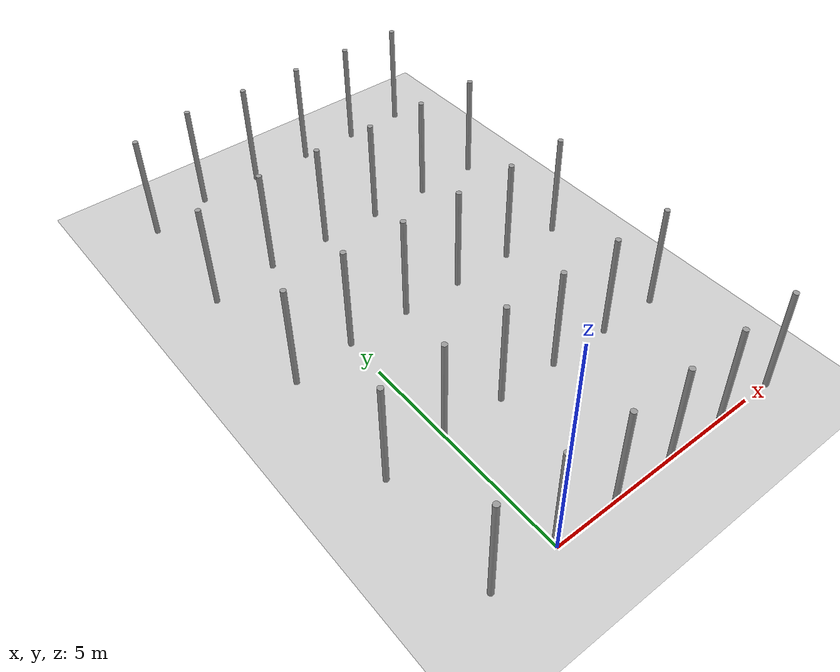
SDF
<sdf version="1.6">
 <world name="default">
  <light name="sun" type="directional">
   <pose>0 0 10 0 -0 0</pose>
   <diffuse>0.8 0.8 0.8 1</diffuse>
   <specular>0.1 0.1 0.1 1</specular>
   <attenuation>
    <range>1000</range>
    <constant>0.9</constant>
    <linear>0.01</linear>
    <quadratic>0.001</quadratic>
   </attenuation>
   <direction>-0.5 0.5 -1</direction>
  </light>
  <model name="ground_plane">
   <static>1</static>
   <link name="link">
    <collision name="collision">
     <geometry><plane><normal>0 0 1</normal><size>100 100</size></plane></geometry>
     <surface><friction><ode><mu>100</mu><mu2>50</mu2></ode></friction></surface>
    </collision>
    <visual name="visual">
     <cast_shadows>0</cast_shadows>
     <geometry><plane><normal>0 0 1</normal><size>100 100</size></plane></geometry>
     <material>
      <script><uri>file://media/materials/scripts/gazebo.material</uri><name>Gazebo/Grey</name></script>
     </material>
    </visual>
   </link>
  </model>
  <gravity>0 0 -9.8</gravity>
  <magnetic_field>6e-06 2.3e-05 -4.2e-05</magnetic_field>
  <atmosphere type="adiabatic"/>
  <physics name="default_physics" default="0" type="ode">
   <max_step_size>0.001</max_step_size>
   <real_time_factor>1</real_time_factor>
   <real_time_update_rate>1000</real_time_update_rate>
  </physics>
  <scene><ambient>0.4 0.4 0.4 1</ambient><background>0.7 0.7 0.7 1</background><shadows>1</shadows></scene>
  <spherical_coordinates>
   <surface_model>EARTH_WGS84</surface_model>
   <latitude_deg>0</latitude_deg>
   <longitude_deg>0</longitude_deg>
   <elevation>0</elevation>
   <heading_deg>0</heading_deg>
  </spherical_coordinates>
  <model name="pole_8">
   <link name="link_0">
    <inertial>
     <mass>0.0364582</mass>
     <inertia>
      <ixx>0.00312124</ixx>
      <ixy>0</ixy>
      <ixz>0</ixz>
      <iyy>0.00312124</iyy>
      <iyz>0</iyz>
      <izz>0.00016615</izz>
     </inertia>
    </inertial>
    <visual name="visual">
     <geometry><cylinder><radius>0.06</radius><length>2.5</length></cylinder></geometry>
     <material>
      <lighting>1</lighting>
      <script><uri>file://media/materials/scripts/gazebo.material</uri><name>Gazebo/Grey</name></script>
      <ambient>0.3 0.3 0.3 1</ambient>
      <diffuse>0.7 0.7 0.7 1</diffuse>
      <specular>0.01 0.01 0.01 1</specular>
      <emissive>0 0 0 1</emissive>
      <shader type="vertex"><normal_map>__default__</normal_map></shader>
     </material>
    </visual>
    <collision name="collision">
     <geometry><cylinder><radius>0.06</radius><length>2.5</length></cylinder></geometry>
     <surface>
      <friction>
       <ode><mu>1</mu><mu2>1</mu2><fdir1>0 0 0</fdir1><slip1>0</slip1><slip2>0</slip2></ode>
       <torsional>
        <coefficient>1</coefficient>
        <patch_radius>0</patch_radius>
        <surface_radius>0</surface_radius>
        <use_patch_radius>1</use_patch_radius>
        <ode><slip>0</slip></ode>
       </torsional>
      </friction>
      <bounce><restitution_coefficient>0</restitution_coefficient><threshold>1e+06</threshold></bounce>
      <contact>
       <collide_without_contact>0</collide_without_contact>
       <collide_without_contact_bitmask>1</collide_without_contact_bitmask>
       <collide_bitmask>1</collide_bitmask>
       <ode>
        <soft_cfm>0</soft_cfm>
        <soft_erp>0.2</soft_erp>
        <kp>1e+13</kp>
        <kd>1</kd>
        <max_vel>0.01</max_vel>
        <min_depth>0</min_depth>
       </ode>
       <bullet>
        <split_impulse>1</split_impulse>
        <split_impulse_penetration_threshold>-0.01</split_impulse_penetration_threshold>
        <soft_cfm>0</soft_cfm>
        <soft_erp>0.2</soft_erp>
        <kp>1e+13</kp>
        <kd>1</kd>
       </bullet>
      </contact>
     </surface>
    </collision>
   </link>
   <static>0</static>
   <pose>1.40423 0.001598 1.25 -1e-06 -0 -0.019182</pose>
  </model>
  <model name="pole_9">
   <link name="link_0">
    <inertial>
     <mass>0.0364582</mass>
     <inertia>
      <ixx>0.00312124</ixx>
      <ixy>0</ixy>
      <ixz>0</ixz>
      <iyy>0.00312124</iyy>
      <iyz>0</iyz>
      <izz>0.00016615</izz>
     </inertia>
    </inertial>
    <visual name="visual">
     <geometry><cylinder><radius>0.06</radius><length>2.5</length></cylinder></geometry>
     <material>
      <lighting>1</lighting>
      <script><uri>file://media/materials/scripts/gazebo.material</uri><name>Gazebo/Grey</name></script>
      <ambient>0.3 0.3 0.3 1</ambient>
      <diffuse>0.7 0.7 0.7 1</diffuse>
      <specular>0.01 0.01 0.01 1</specular>
      <emissive>0 0 0 1</emissive>
      <shader type="vertex"><normal_map>__default__</normal_map></shader>
     </material>
    </visual>
    <collision name="collision">
     <geometry><cylinder><radius>0.06</radius><length>2.5</length></cylinder></geometry>
     <surface>
      <friction>
       <ode><mu>1</mu><mu2>1</mu2><fdir1>0 0 0</fdir1><slip1>0</slip1><slip2>0</slip2></ode>
       <torsional>
        <coefficient>1</coefficient>
        <patch_radius>0</patch_radius>
        <surface_radius>0</surface_radius>
        <use_patch_radius>1</use_patch_radius>
        <ode><slip>0</slip></ode>
       </torsional>
      </friction>
      <bounce><restitution_coefficient>0</restitution_coefficient><threshold>1e+06</threshold></bounce>
      <contact>
       <collide_without_contact>0</collide_without_contact>
       <collide_without_contact_bitmask>1</collide_without_contact_bitmask>
       <collide_bitmask>1</collide_bitmask>
       <ode>
        <soft_cfm>0</soft_cfm>
        <soft_erp>0.2</soft_erp>
        <kp>1e+13</kp>
        <kd>1</kd>
        <max_vel>0.01</max_vel>
        <min_depth>0</min_depth>
       </ode>
       <bullet>
        <split_impulse>1</split_impulse>
        <split_impulse_penetration_threshold>-0.01</split_impulse_penetration_threshold>
        <soft_cfm>0</soft_cfm>
        <soft_erp>0.2</soft_erp>
        <kp>1e+13</kp>
        <kd>1</kd>
       </bullet>
      </contact>
     </surface>
    </collision>
   </link>
   <static>0</static>
   <pose>2.80804 0.001723 1.24999 -1e-06 1e-06 -0.038445</pose>
  </model>
  <model name="pole_10">
   <link name="link_0">
    <inertial>
     <mass>0.0364582</mass>
     <inertia>
      <ixx>0.00312124</ixx>
      <ixy>0</ixy>
      <ixz>0</ixz>
      <iyy>0.00312124</iyy>
      <iyz>0</iyz>
      <izz>0.00016615</izz>
     </inertia>
    </inertial>
    <visual name="visual">
     <geometry><cylinder><radius>0.06</radius><length>2.5</length></cylinder></geometry>
     <material>
      <lighting>1</lighting>
      <script><uri>file://media/materials/scripts/gazebo.material</uri><name>Gazebo/Grey</name></script>
      <ambient>0.3 0.3 0.3 1</ambient>
      <diffuse>0.7 0.7 0.7 1</diffuse>
      <specular>0.01 0.01 0.01 1</specular>
      <emissive>0 0 0 1</emissive>
      <shader type="vertex"><normal_map>__default__</normal_map></shader>
     </material>
    </visual>
    <collision name="collision">
     <geometry><cylinder><radius>0.06</radius><length>2.5</length></cylinder></geometry>
     <surface>
      <friction>
       <ode><mu>1</mu><mu2>1</mu2><fdir1>0 0 0</fdir1><slip1>0</slip1><slip2>0</slip2></ode>
       <torsional>
        <coefficient>1</coefficient>
        <patch_radius>0</patch_radius>
        <surface_radius>0</surface_radius>
        <use_patch_radius>1</use_patch_radius>
        <ode><slip>0</slip></ode>
       </torsional>
      </friction>
      <bounce><restitution_coefficient>0</restitution_coefficient><threshold>1e+06</threshold></bounce>
      <contact>
       <collide_without_contact>0</collide_without_contact>
       <collide_without_contact_bitmask>1</collide_without_contact_bitmask>
       <collide_bitmask>1</collide_bitmask>
       <ode>
        <soft_cfm>0</soft_cfm>
        <soft_erp>0.2</soft_erp>
        <kp>1e+13</kp>
        <kd>1</kd>
        <max_vel>0.01</max_vel>
        <min_depth>0</min_depth>
       </ode>
       <bullet>
        <split_impulse>1</split_impulse>
        <split_impulse_penetration_threshold>-0.01</split_impulse_penetration_threshold>
        <soft_cfm>0</soft_cfm>
        <soft_erp>0.2</soft_erp>
        <kp>1e+13</kp>
        <kd>1</kd>
       </bullet>
      </contact>
     </surface>
    </collision>
   </link>
   <static>0</static>
   <pose>4.20396 0.001667 1.25 -1e-06 -1e-06 -0.02158</pose>
  </model>
  <model name="pole_11">
   <link name="link_0">
    <inertial>
     <mass>0.0364582</mass>
     <inertia>
      <ixx>0.00312124</ixx>
      <ixy>0</ixy>
      <ixz>0</ixz>
      <iyy>0.00312124</iyy>
      <iyz>0</iyz>
      <izz>0.00016615</izz>
     </inertia>
    </inertial>
    <visual name="visual">
     <geometry><cylinder><radius>0.06</radius><length>2.5</length></cylinder></geometry>
     <material>
      <lighting>1</lighting>
      <script><uri>file://media/materials/scripts/gazebo.material</uri><name>Gazebo/Grey</name></script>
      <ambient>0.3 0.3 0.3 1</ambient>
      <diffuse>0.7 0.7 0.7 1</diffuse>
      <specular>0.01 0.01 0.01 1</specular>
      <emissive>0 0 0 1</emissive>
      <shader type="vertex"><normal_map>__default__</normal_map></shader>
     </material>
    </visual>
    <collision name="collision">
     <geometry><cylinder><radius>0.06</radius><length>2.5</length></cylinder></geometry>
     <surface>
      <friction>
       <ode><mu>1</mu><mu2>1</mu2><fdir1>0 0 0</fdir1><slip1>0</slip1><slip2>0</slip2></ode>
       <torsional>
        <coefficient>1</coefficient>
        <patch_radius>0</patch_radius>
        <surface_radius>0</surface_radius>
        <use_patch_radius>1</use_patch_radius>
        <ode><slip>0</slip></ode>
       </torsional>
      </friction>
      <bounce><restitution_coefficient>0</restitution_coefficient><threshold>1e+06</threshold></bounce>
      <contact>
       <collide_without_contact>0</collide_without_contact>
       <collide_without_contact_bitmask>1</collide_without_contact_bitmask>
       <collide_bitmask>1</collide_bitmask>
       <ode>
        <soft_cfm>0</soft_cfm>
        <soft_erp>0.2</soft_erp>
        <kp>1e+13</kp>
        <kd>1</kd>
        <max_vel>0.01</max_vel>
        <min_depth>0</min_depth>
       </ode>
       <bullet>
        <split_impulse>1</split_impulse>
        <split_impulse_penetration_threshold>-0.01</split_impulse_penetration_threshold>
        <soft_cfm>0</soft_cfm>
        <soft_erp>0.2</soft_erp>
        <kp>1e+13</kp>
        <kd>1</kd>
       </bullet>
      </contact>
     </surface>
    </collision>
   </link>
   <static>0</static>
   <pose>5.61625 0.00154 1.25 -1e-06 1e-06 -0.022011</pose>
  </model>
  <model name="pole_11_clone">
   <link name="link_0">
    <inertial>
     <mass>0.0364582</mass>
     <inertia>
      <ixx>0.00312124</ixx>
      <ixy>0</ixy>
      <ixz>0</ixz>
      <iyy>0.00312124</iyy>
      <iyz>0</iyz>
      <izz>0.00016615</izz>
     </inertia>
    </inertial>
    <visual name="visual">
     <geometry><cylinder><radius>0.06</radius><length>2.5</length></cylinder></geometry>
     <material>
      <lighting>1</lighting>
      <script><uri>file://media/materials/scripts/gazebo.material</uri><name>Gazebo/Grey</name></script>
      <ambient>0.3 0.3 0.3 1</ambient>
      <diffuse>0.7 0.7 0.7 1</diffuse>
      <specular>0.01 0.01 0.01 1</specular>
      <emissive>0 0 0 1</emissive>
      <shader type="vertex"><normal_map>__default__</normal_map></shader>
     </material>
    </visual>
    <collision name="collision">
     <geometry><cylinder><radius>0.06</radius><length>2.5</length></cylinder></geometry>
     <surface>
      <friction>
       <ode><mu>1</mu><mu2>1</mu2><fdir1>0 0 0</fdir1><slip1>0</slip1><slip2>0</slip2></ode>
       <torsional>
        <coefficient>1</coefficient>
        <patch_radius>0</patch_radius>
        <surface_radius>0</surface_radius>
        <use_patch_radius>1</use_patch_radius>
        <ode><slip>0</slip></ode>
       </torsional>
      </friction>
      <bounce><restitution_coefficient>0</restitution_coefficient><threshold>1e+06</threshold></bounce>
      <contact>
       <collide_without_contact>0</collide_without_contact>
       <collide_without_contact_bitmask>1</collide_without_contact_bitmask>
       <collide_bitmask>1</collide_bitmask>
       <ode>
        <soft_cfm>0</soft_cfm>
        <soft_erp>0.2</soft_erp>
        <kp>1e+13</kp>
        <kd>1</kd>
        <max_vel>0.01</max_vel>
        <min_depth>0</min_depth>
       </ode>
       <bullet>
        <split_impulse>1</split_impulse>
        <split_impulse_penetration_threshold>-0.01</split_impulse_penetration_threshold>
        <soft_cfm>0</soft_cfm>
        <soft_erp>0.2</soft_erp>
        <kp>1e+13</kp>
        <kd>1</kd>
       </bullet>
      </contact>
     </surface>
    </collision>
   </link>
   <static>0</static>
   <pose>0.000719 2.98383 1.25 -1e-06 1e-06 -0.028489</pose>
  </model>
  <model name="pole">
   <link name="link_0">
    <inertial>
     <mass>0.0364582</mass>
     <inertia>
      <ixx>0.00312124</ixx>
      <ixy>0</ixy>
      <ixz>0</ixz>
      <iyy>0.00312124</iyy>
      <iyz>0</iyz>
      <izz>0.00016615</izz>
     </inertia>
    </inertial>
    <visual name="visual">
     <geometry><cylinder><radius>0.06</radius><length>2.5</length></cylinder></geometry>
     <material>
      <lighting>1</lighting>
      <script><uri>file://media/materials/scripts/gazebo.material</uri><name>Gazebo/Grey</name></script>
      <ambient>0.3 0.3 0.3 1</ambient>
      <diffuse>0.7 0.7 0.7 1</diffuse>
      <specular>0.01 0.01 0.01 1</specular>
      <emissive>0 0 0 1</emissive>
      <shader type="vertex"><normal_map>__default__</normal_map></shader>
     </material>
    </visual>
    <collision name="collision">
     <geometry><cylinder><radius>0.06</radius><length>2.5</length></cylinder></geometry>
     <surface>
      <friction>
       <ode><mu>1</mu><mu2>1</mu2><fdir1>0 0 0</fdir1><slip1>0</slip1><slip2>0</slip2></ode>
       <torsional>
        <coefficient>1</coefficient>
        <patch_radius>0</patch_radius>
        <surface_radius>0</surface_radius>
        <use_patch_radius>1</use_patch_radius>
        <ode><slip>0</slip></ode>
       </torsional>
      </friction>
      <bounce><restitution_coefficient>0</restitution_coefficient><threshold>1e+06</threshold></bounce>
      <contact>
       <collide_without_contact>0</collide_without_contact>
       <collide_without_contact_bitmask>1</collide_without_contact_bitmask>
       <collide_bitmask>1</collide_bitmask>
       <ode>
        <soft_cfm>0</soft_cfm>
        <soft_erp>0.2</soft_erp>
        <kp>1e+13</kp>
        <kd>1</kd>
        <max_vel>0.01</max_vel>
        <min_depth>0</min_depth>
       </ode>
       <bullet>
        <split_impulse>1</split_impulse>
        <split_impulse_penetration_threshold>-0.01</split_impulse_penetration_threshold>
        <soft_cfm>0</soft_cfm>
        <soft_erp>0.2</soft_erp>
        <kp>1e+13</kp>
        <kd>1</kd>
       </bullet>
      </contact>
     </surface>
    </collision>
   </link>
   <static>0</static>
   <pose>0.006726 5.96138 1.24999 0 0 -0.017728</pose>
  </model>
  <model name="pole_0">
   <link name="link_0">
    <inertial>
     <mass>0.0364582</mass>
     <inertia>
      <ixx>0.00312124</ixx>
      <ixy>0</ixy>
      <ixz>0</ixz>
      <iyy>0.00312124</iyy>
      <iyz>0</iyz>
      <izz>0.00016615</izz>
     </inertia>
    </inertial>
    <visual name="visual">
     <geometry><cylinder><radius>0.06</radius><length>2.5</length></cylinder></geometry>
     <material>
      <lighting>1</lighting>
      <script><uri>file://media/materials/scripts/gazebo.material</uri><name>Gazebo/Grey</name></script>
      <ambient>0.3 0.3 0.3 1</ambient>
      <diffuse>0.7 0.7 0.7 1</diffuse>
      <specular>0.01 0.01 0.01 1</specular>
      <emissive>0 0 0 1</emissive>
      <shader type="vertex"><normal_map>__default__</normal_map></shader>
     </material>
    </visual>
    <collision name="collision">
     <geometry><cylinder><radius>0.06</radius><length>2.5</length></cylinder></geometry>
     <surface>
      <friction>
       <ode><mu>1</mu><mu2>1</mu2><fdir1>0 0 0</fdir1><slip1>0</slip1><slip2>0</slip2></ode>
       <torsional>
        <coefficient>1</coefficient>
        <patch_radius>0</patch_radius>
        <surface_radius>0</surface_radius>
        <use_patch_radius>1</use_patch_radius>
        <ode><slip>0</slip></ode>
       </torsional>
      </friction>
      <bounce><restitution_coefficient>0</restitution_coefficient><threshold>1e+06</threshold></bounce>
      <contact>
       <collide_without_contact>0</collide_without_contact>
       <collide_without_contact_bitmask>1</collide_without_contact_bitmask>
       <collide_bitmask>1</collide_bitmask>
       <ode>
        <soft_cfm>0</soft_cfm>
        <soft_erp>0.2</soft_erp>
        <kp>1e+13</kp>
        <kd>1</kd>
        <max_vel>0.01</max_vel>
        <min_depth>0</min_depth>
       </ode>
       <bullet>
        <split_impulse>1</split_impulse>
        <split_impulse_penetration_threshold>-0.01</split_impulse_penetration_threshold>
        <soft_cfm>0</soft_cfm>
        <soft_erp>0.2</soft_erp>
        <kp>1e+13</kp>
        <kd>1</kd>
       </bullet>
      </contact>
     </surface>
    </collision>
   </link>
   <static>0</static>
   <pose>0.013523 8.94152 1.25 -1e-06 1e-06 -0.020059</pose>
  </model>
  <model name="pole_1">
   <link name="link_0">
    <inertial>
     <mass>0.0364582</mass>
     <inertia>
      <ixx>0.00312124</ixx>
      <ixy>0</ixy>
      <ixz>0</ixz>
      <iyy>0.00312124</iyy>
      <iyz>0</iyz>
      <izz>0.00016615</izz>
     </inertia>
    </inertial>
    <visual name="visual">
     <geometry><cylinder><radius>0.06</radius><length>2.5</length></cylinder></geometry>
     <material>
      <lighting>1</lighting>
      <script><uri>file://media/materials/scripts/gazebo.material</uri><name>Gazebo/Grey</name></script>
      <ambient>0.3 0.3 0.3 1</ambient>
      <diffuse>0.7 0.7 0.7 1</diffuse>
      <specular>0.01 0.01 0.01 1</specular>
      <emissive>0 0 0 1</emissive>
      <shader type="vertex"><normal_map>__default__</normal_map></shader>
     </material>
    </visual>
    <collision name="collision">
     <geometry><cylinder><radius>0.06</radius><length>2.5</length></cylinder></geometry>
     <surface>
      <friction>
       <ode><mu>1</mu><mu2>1</mu2><fdir1>0 0 0</fdir1><slip1>0</slip1><slip2>0</slip2></ode>
       <torsional>
        <coefficient>1</coefficient>
        <patch_radius>0</patch_radius>
        <surface_radius>0</surface_radius>
        <use_patch_radius>1</use_patch_radius>
        <ode><slip>0</slip></ode>
       </torsional>
      </friction>
      <bounce><restitution_coefficient>0</restitution_coefficient><threshold>1e+06</threshold></bounce>
      <contact>
       <collide_without_contact>0</collide_without_contact>
       <collide_without_contact_bitmask>1</collide_without_contact_bitmask>
       <collide_bitmask>1</collide_bitmask>
       <ode>
        <soft_cfm>0</soft_cfm>
        <soft_erp>0.2</soft_erp>
        <kp>1e+13</kp>
        <kd>1</kd>
        <max_vel>0.01</max_vel>
        <min_depth>0</min_depth>
       </ode>
       <bullet>
        <split_impulse>1</split_impulse>
        <split_impulse_penetration_threshold>-0.01</split_impulse_penetration_threshold>
        <soft_cfm>0</soft_cfm>
        <soft_erp>0.2</soft_erp>
        <kp>1e+13</kp>
        <kd>1</kd>
       </bullet>
      </contact>
     </surface>
    </collision>
   </link>
   <static>0</static>
   <pose>-0.008094 11.9213 1.24999 0 -2e-06 -0.020086</pose>
  </model>
  <model name="pole_2">
   <link name="link_0">
    <inertial>
     <mass>0.0364582</mass>
     <inertia>
      <ixx>0.00312124</ixx>
      <ixy>0</ixy>
      <ixz>0</ixz>
      <iyy>0.00312124</iyy>
      <iyz>0</iyz>
      <izz>0.00016615</izz>
     </inertia>
    </inertial>
    <visual name="visual">
     <geometry><cylinder><radius>0.06</radius><length>2.5</length></cylinder></geometry>
     <material>
      <lighting>1</lighting>
      <script><uri>file://media/materials/scripts/gazebo.material</uri><name>Gazebo/Grey</name></script>
      <ambient>0.3 0.3 0.3 1</ambient>
      <diffuse>0.7 0.7 0.7 1</diffuse>
      <specular>0.01 0.01 0.01 1</specular>
      <emissive>0 0 0 1</emissive>
      <shader type="vertex"><normal_map>__default__</normal_map></shader>
     </material>
    </visual>
    <collision name="collision">
     <geometry><cylinder><radius>0.06</radius><length>2.5</length></cylinder></geometry>
     <surface>
      <friction>
       <ode><mu>1</mu><mu2>1</mu2><fdir1>0 0 0</fdir1><slip1>0</slip1><slip2>0</slip2></ode>
       <torsional>
        <coefficient>1</coefficient>
        <patch_radius>0</patch_radius>
        <surface_radius>0</surface_radius>
        <use_patch_radius>1</use_patch_radius>
        <ode><slip>0</slip></ode>
       </torsional>
      </friction>
      <bounce><restitution_coefficient>0</restitution_coefficient><threshold>1e+06</threshold></bounce>
      <contact>
       <collide_without_contact>0</collide_without_contact>
       <collide_without_contact_bitmask>1</collide_without_contact_bitmask>
       <collide_bitmask>1</collide_bitmask>
       <ode>
        <soft_cfm>0</soft_cfm>
        <soft_erp>0.2</soft_erp>
        <kp>1e+13</kp>
        <kd>1</kd>
        <max_vel>0.01</max_vel>
        <min_depth>0</min_depth>
       </ode>
       <bullet>
        <split_impulse>1</split_impulse>
        <split_impulse_penetration_threshold>-0.01</split_impulse_penetration_threshold>
        <soft_cfm>0</soft_cfm>
        <soft_erp>0.2</soft_erp>
        <kp>1e+13</kp>
        <kd>1</kd>
       </bullet>
      </contact>
     </surface>
    </collision>
   </link>
   <static>0</static>
   <pose>0.034218 0.094388 1.24999 1e-06 -1e-06 0.045522</pose>
  </model>
  <model name="pole_3">
   <link name="link_0">
    <inertial>
     <mass>0.0364582</mass>
     <inertia>
      <ixx>0.00312124</ixx>
      <ixy>0</ixy>
      <ixz>0</ixz>
      <iyy>0.00312124</iyy>
      <iyz>0</iyz>
      <izz>0.00016615</izz>
     </inertia>
    </inertial>
    <visual name="visual">
     <geometry><cylinder><radius>0.06</radius><length>2.5</length></cylinder></geometry>
     <material>
      <lighting>1</lighting>
      <script><uri>file://media/materials/scripts/gazebo.material</uri><name>Gazebo/Grey</name></script>
      <ambient>0.3 0.3 0.3 1</ambient>
      <diffuse>0.7 0.7 0.7 1</diffuse>
      <specular>0.01 0.01 0.01 1</specular>
      <emissive>0 0 0 1</emissive>
      <shader type="vertex"><normal_map>__default__</normal_map></shader>
     </material>
    </visual>
    <collision name="collision">
     <geometry><cylinder><radius>0.06</radius><length>2.5</length></cylinder></geometry>
     <surface>
      <friction>
       <ode><mu>1</mu><mu2>1</mu2><fdir1>0 0 0</fdir1><slip1>0</slip1><slip2>0</slip2></ode>
       <torsional>
        <coefficient>1</coefficient>
        <patch_radius>0</patch_radius>
        <surface_radius>0</surface_radius>
        <use_patch_radius>1</use_patch_radius>
        <ode><slip>0</slip></ode>
       </torsional>
      </friction>
      <bounce><restitution_coefficient>0</restitution_coefficient><threshold>1e+06</threshold></bounce>
      <contact>
       <collide_without_contact>0</collide_without_contact>
       <collide_without_contact_bitmask>1</collide_without_contact_bitmask>
       <collide_bitmask>1</collide_bitmask>
       <ode>
        <soft_cfm>0</soft_cfm>
        <soft_erp>0.2</soft_erp>
        <kp>1e+13</kp>
        <kd>1</kd>
        <max_vel>0.01</max_vel>
        <min_depth>0</min_depth>
       </ode>
       <bullet>
        <split_impulse>1</split_impulse>
        <split_impulse_penetration_threshold>-0.01</split_impulse_penetration_threshold>
        <soft_cfm>0</soft_cfm>
        <soft_erp>0.2</soft_erp>
        <kp>1e+13</kp>
        <kd>1</kd>
       </bullet>
      </contact>
     </surface>
    </collision>
   </link>
   <static>0</static>
   <pose>1.40473 2.98134 1.25 -1e-06 -1e-06 -0.015175</pose>
  </model>
  <model name="pole_5">
   <link name="link_0">
    <inertial>
     <mass>0.0364582</mass>
     <inertia>
      <ixx>0.00312124</ixx>
      <ixy>0</ixy>
      <ixz>0</ixz>
      <iyy>0.00312124</iyy>
      <iyz>0</iyz>
      <izz>0.00016615</izz>
     </inertia>
    </inertial>
    <visual name="visual">
     <geometry><cylinder><radius>0.06</radius><length>2.5</length></cylinder></geometry>
     <material>
      <lighting>1</lighting>
      <script><uri>file://media/materials/scripts/gazebo.material</uri><name>Gazebo/Grey</name></script>
      <ambient>0.3 0.3 0.3 1</ambient>
      <diffuse>0.7 0.7 0.7 1</diffuse>
      <specular>0.01 0.01 0.01 1</specular>
      <emissive>0 0 0 1</emissive>
      <shader type="vertex"><normal_map>__default__</normal_map></shader>
     </material>
    </visual>
    <collision name="collision">
     <geometry><cylinder><radius>0.06</radius><length>2.5</length></cylinder></geometry>
     <surface>
      <friction>
       <ode><mu>1</mu><mu2>1</mu2><fdir1>0 0 0</fdir1><slip1>0</slip1><slip2>0</slip2></ode>
       <torsional>
        <coefficient>1</coefficient>
        <patch_radius>0</patch_radius>
        <surface_radius>0</surface_radius>
        <use_patch_radius>1</use_patch_radius>
        <ode><slip>0</slip></ode>
       </torsional>
      </friction>
      <bounce><restitution_coefficient>0</restitution_coefficient><threshold>1e+06</threshold></bounce>
      <contact>
       <collide_without_contact>0</collide_without_contact>
       <collide_without_contact_bitmask>1</collide_without_contact_bitmask>
       <collide_bitmask>1</collide_bitmask>
       <ode>
        <soft_cfm>0</soft_cfm>
        <soft_erp>0.2</soft_erp>
        <kp>1e+13</kp>
        <kd>1</kd>
        <max_vel>0.01</max_vel>
        <min_depth>0</min_depth>
       </ode>
       <bullet>
        <split_impulse>1</split_impulse>
        <split_impulse_penetration_threshold>-0.01</split_impulse_penetration_threshold>
        <soft_cfm>0</soft_cfm>
        <soft_erp>0.2</soft_erp>
        <kp>1e+13</kp>
        <kd>1</kd>
       </bullet>
      </contact>
     </surface>
    </collision>
   </link>
   <static>0</static>
   <pose>2.79584 2.98123 1.25 -1e-06 1e-06 -0.015543</pose>
  </model>
  <model name="pole_6">
   <link name="link_0">
    <inertial>
     <mass>0.0364582</mass>
     <inertia>
      <ixx>0.00312124</ixx>
      <ixy>0</ixy>
      <ixz>0</ixz>
      <iyy>0.00312124</iyy>
      <iyz>0</iyz>
      <izz>0.00016615</izz>
     </inertia>
    </inertial>
    <visual name="visual">
     <geometry><cylinder><radius>0.06</radius><length>2.5</length></cylinder></geometry>
     <material>
      <lighting>1</lighting>
      <script><uri>file://media/materials/scripts/gazebo.material</uri><name>Gazebo/Grey</name></script>
      <ambient>0.3 0.3 0.3 1</ambient>
      <diffuse>0.7 0.7 0.7 1</diffuse>
      <specular>0.01 0.01 0.01 1</specular>
      <emissive>0 0 0 1</emissive>
      <shader type="vertex"><normal_map>__default__</normal_map></shader>
     </material>
    </visual>
    <collision name="collision">
     <geometry><cylinder><radius>0.06</radius><length>2.5</length></cylinder></geometry>
     <surface>
      <friction>
       <ode><mu>1</mu><mu2>1</mu2><fdir1>0 0 0</fdir1><slip1>0</slip1><slip2>0</slip2></ode>
       <torsional>
        <coefficient>1</coefficient>
        <patch_radius>0</patch_radius>
        <surface_radius>0</surface_radius>
        <use_patch_radius>1</use_patch_radius>
        <ode><slip>0</slip></ode>
       </torsional>
      </friction>
      <bounce><restitution_coefficient>0</restitution_coefficient><threshold>1e+06</threshold></bounce>
      <contact>
       <collide_without_contact>0</collide_without_contact>
       <collide_without_contact_bitmask>1</collide_without_contact_bitmask>
       <collide_bitmask>1</collide_bitmask>
       <ode>
        <soft_cfm>0</soft_cfm>
        <soft_erp>0.2</soft_erp>
        <kp>1e+13</kp>
        <kd>1</kd>
        <max_vel>0.01</max_vel>
        <min_depth>0</min_depth>
       </ode>
       <bullet>
        <split_impulse>1</split_impulse>
        <split_impulse_penetration_threshold>-0.01</split_impulse_penetration_threshold>
        <soft_cfm>0</soft_cfm>
        <soft_erp>0.2</soft_erp>
        <kp>1e+13</kp>
        <kd>1</kd>
       </bullet>
      </contact>
     </surface>
    </collision>
   </link>
   <static>0</static>
   <pose>4.22241 2.98115 1.24999 1e-06 -2e-06 -0.014109</pose>
  </model>
  <model name="pole_7">
   <link name="link_0">
    <inertial>
     <mass>0.0364582</mass>
     <inertia>
      <ixx>0.00312124</ixx>
      <ixy>0</ixy>
      <ixz>0</ixz>
      <iyy>0.00312124</iyy>
      <iyz>0</iyz>
      <izz>0.00016615</izz>
     </inertia>
    </inertial>
    <visual name="visual">
     <geometry><cylinder><radius>0.06</radius><length>2.5</length></cylinder></geometry>
     <material>
      <lighting>1</lighting>
      <script><uri>file://media/materials/scripts/gazebo.material</uri><name>Gazebo/Grey</name></script>
      <ambient>0.3 0.3 0.3 1</ambient>
      <diffuse>0.7 0.7 0.7 1</diffuse>
      <specular>0.01 0.01 0.01 1</specular>
      <emissive>0 0 0 1</emissive>
      <shader type="vertex"><normal_map>__default__</normal_map></shader>
     </material>
    </visual>
    <collision name="collision">
     <geometry><cylinder><radius>0.06</radius><length>2.5</length></cylinder></geometry>
     <surface>
      <friction>
       <ode><mu>1</mu><mu2>1</mu2><fdir1>0 0 0</fdir1><slip1>0</slip1><slip2>0</slip2></ode>
       <torsional>
        <coefficient>1</coefficient>
        <patch_radius>0</patch_radius>
        <surface_radius>0</surface_radius>
        <use_patch_radius>1</use_patch_radius>
        <ode><slip>0</slip></ode>
       </torsional>
      </friction>
      <bounce><restitution_coefficient>0</restitution_coefficient><threshold>1e+06</threshold></bounce>
      <contact>
       <collide_without_contact>0</collide_without_contact>
       <collide_without_contact_bitmask>1</collide_without_contact_bitmask>
       <collide_bitmask>1</collide_bitmask>
       <ode>
        <soft_cfm>0</soft_cfm>
        <soft_erp>0.2</soft_erp>
        <kp>1e+13</kp>
        <kd>1</kd>
        <max_vel>0.01</max_vel>
        <min_depth>0</min_depth>
       </ode>
       <bullet>
        <split_impulse>1</split_impulse>
        <split_impulse_penetration_threshold>-0.01</split_impulse_penetration_threshold>
        <soft_cfm>0</soft_cfm>
        <soft_erp>0.2</soft_erp>
        <kp>1e+13</kp>
        <kd>1</kd>
       </bullet>
      </contact>
     </surface>
    </collision>
   </link>
   <static>0</static>
   <pose>5.60736 2.98123 1.24999 0 1e-06 -0.014927</pose>
  </model>
  <model name="pole_12">
   <link name="link_0">
    <inertial>
     <mass>0.0364582</mass>
     <inertia>
      <ixx>0.00312124</ixx>
      <ixy>0</ixy>
      <ixz>0</ixz>
      <iyy>0.00312124</iyy>
      <iyz>0</iyz>
      <izz>0.00016615</izz>
     </inertia>
    </inertial>
    <visual name="visual">
     <geometry><cylinder><radius>0.06</radius><length>2.5</length></cylinder></geometry>
     <material>
      <lighting>1</lighting>
      <script><uri>file://media/materials/scripts/gazebo.material</uri><name>Gazebo/Grey</name></script>
      <ambient>0.3 0.3 0.3 1</ambient>
      <diffuse>0.7 0.7 0.7 1</diffuse>
      <specular>0.01 0.01 0.01 1</specular>
      <emissive>0 0 0 1</emissive>
      <shader type="vertex"><normal_map>__default__</normal_map></shader>
     </material>
    </visual>
    <collision name="collision">
     <geometry><cylinder><radius>0.06</radius><length>2.5</length></cylinder></geometry>
     <surface>
      <friction>
       <ode><mu>1</mu><mu2>1</mu2><fdir1>0 0 0</fdir1><slip1>0</slip1><slip2>0</slip2></ode>
       <torsional>
        <coefficient>1</coefficient>
        <patch_radius>0</patch_radius>
        <surface_radius>0</surface_radius>
        <use_patch_radius>1</use_patch_radius>
        <ode><slip>0</slip></ode>
       </torsional>
      </friction>
      <bounce><restitution_coefficient>0</restitution_coefficient><threshold>1e+06</threshold></bounce>
      <contact>
       <collide_without_contact>0</collide_without_contact>
       <collide_without_contact_bitmask>1</collide_without_contact_bitmask>
       <collide_bitmask>1</collide_bitmask>
       <ode>
        <soft_cfm>0</soft_cfm>
        <soft_erp>0.2</soft_erp>
        <kp>1e+13</kp>
        <kd>1</kd>
        <max_vel>0.01</max_vel>
        <min_depth>0</min_depth>
       </ode>
       <bullet>
        <split_impulse>1</split_impulse>
        <split_impulse_penetration_threshold>-0.01</split_impulse_penetration_threshold>
        <soft_cfm>0</soft_cfm>
        <soft_erp>0.2</soft_erp>
        <kp>1e+13</kp>
        <kd>1</kd>
       </bullet>
      </contact>
     </surface>
    </collision>
   </link>
   <static>0</static>
   <pose>1.41362 5.96122 1.25 -1e-06 -1e-06 -0.011753</pose>
  </model>
  <model name="pole_13">
   <link name="link_0">
    <inertial>
     <mass>0.0364582</mass>
     <inertia>
      <ixx>0.00312124</ixx>
      <ixy>0</ixy>
      <ixz>0</ixz>
      <iyy>0.00312124</iyy>
      <iyz>0</iyz>
      <izz>0.00016615</izz>
     </inertia>
    </inertial>
    <visual name="visual">
     <geometry><cylinder><radius>0.06</radius><length>2.5</length></cylinder></geometry>
     <material>
      <lighting>1</lighting>
      <script><uri>file://media/materials/scripts/gazebo.material</uri><name>Gazebo/Grey</name></script>
      <ambient>0.3 0.3 0.3 1</ambient>
      <diffuse>0.7 0.7 0.7 1</diffuse>
      <specular>0.01 0.01 0.01 1</specular>
      <emissive>0 0 0 1</emissive>
      <shader type="vertex"><normal_map>__default__</normal_map></shader>
     </material>
    </visual>
    <collision name="collision">
     <geometry><cylinder><radius>0.06</radius><length>2.5</length></cylinder></geometry>
     <surface>
      <friction>
       <ode><mu>1</mu><mu2>1</mu2><fdir1>0 0 0</fdir1><slip1>0</slip1><slip2>0</slip2></ode>
       <torsional>
        <coefficient>1</coefficient>
        <patch_radius>0</patch_radius>
        <surface_radius>0</surface_radius>
        <use_patch_radius>1</use_patch_radius>
        <ode><slip>0</slip></ode>
       </torsional>
      </friction>
      <bounce><restitution_coefficient>0</restitution_coefficient><threshold>1e+06</threshold></bounce>
      <contact>
       <collide_without_contact>0</collide_without_contact>
       <collide_without_contact_bitmask>1</collide_without_contact_bitmask>
       <collide_bitmask>1</collide_bitmask>
       <ode>
        <soft_cfm>0</soft_cfm>
        <soft_erp>0.2</soft_erp>
        <kp>1e+13</kp>
        <kd>1</kd>
        <max_vel>0.01</max_vel>
        <min_depth>0</min_depth>
       </ode>
       <bullet>
        <split_impulse>1</split_impulse>
        <split_impulse_penetration_threshold>-0.01</split_impulse_penetration_threshold>
        <soft_cfm>0</soft_cfm>
        <soft_erp>0.2</soft_erp>
        <kp>1e+13</kp>
        <kd>1</kd>
       </bullet>
      </contact>
     </surface>
    </collision>
   </link>
   <static>0</static>
   <pose>2.80804 5.96139 1.24999 0 1e-06 -0.012994</pose>
  </model>
  <model name="pole_14">
   <link name="link_0">
    <inertial>
     <mass>0.0364582</mass>
     <inertia>
      <ixx>0.00312124</ixx>
      <ixy>0</ixy>
      <ixz>0</ixz>
      <iyy>0.00312124</iyy>
      <iyz>0</iyz>
      <izz>0.00016615</izz>
     </inertia>
    </inertial>
    <visual name="visual">
     <geometry><cylinder><radius>0.06</radius><length>2.5</length></cylinder></geometry>
     <material>
      <lighting>1</lighting>
      <script><uri>file://media/materials/scripts/gazebo.material</uri><name>Gazebo/Grey</name></script>
      <ambient>0.3 0.3 0.3 1</ambient>
      <diffuse>0.7 0.7 0.7 1</diffuse>
      <specular>0.01 0.01 0.01 1</specular>
      <emissive>0 0 0 1</emissive>
      <shader type="vertex"><normal_map>__default__</normal_map></shader>
     </material>
    </visual>
    <collision name="collision">
     <geometry><cylinder><radius>0.06</radius><length>2.5</length></cylinder></geometry>
     <surface>
      <friction>
       <ode><mu>1</mu><mu2>1</mu2><fdir1>0 0 0</fdir1><slip1>0</slip1><slip2>0</slip2></ode>
       <torsional>
        <coefficient>1</coefficient>
        <patch_radius>0</patch_radius>
        <surface_radius>0</surface_radius>
        <use_patch_radius>1</use_patch_radius>
        <ode><slip>0</slip></ode>
       </torsional>
      </friction>
      <bounce><restitution_coefficient>0</restitution_coefficient><threshold>1e+06</threshold></bounce>
      <contact>
       <collide_without_contact>0</collide_without_contact>
       <collide_without_contact_bitmask>1</collide_without_contact_bitmask>
       <collide_bitmask>1</collide_bitmask>
       <ode>
        <soft_cfm>0</soft_cfm>
        <soft_erp>0.2</soft_erp>
        <kp>1e+13</kp>
        <kd>1</kd>
        <max_vel>0.01</max_vel>
        <min_depth>0</min_depth>
       </ode>
       <bullet>
        <split_impulse>1</split_impulse>
        <split_impulse_penetration_threshold>-0.01</split_impulse_penetration_threshold>
        <soft_cfm>0</soft_cfm>
        <soft_erp>0.2</soft_erp>
        <kp>1e+13</kp>
        <kd>1</kd>
       </bullet>
      </contact>
     </surface>
    </collision>
   </link>
   <static>0</static>
   <pose>4.21952 5.96117 1.24999 -0 4e-06 -0.012826</pose>
  </model>
  <model name="pole_15">
   <link name="link_0">
    <inertial>
     <mass>0.0364582</mass>
     <inertia>
      <ixx>0.00312124</ixx>
      <ixy>0</ixy>
      <ixz>0</ixz>
      <iyy>0.00312124</iyy>
      <iyz>0</iyz>
      <izz>0.00016615</izz>
     </inertia>
    </inertial>
    <visual name="visual">
     <geometry><cylinder><radius>0.06</radius><length>2.5</length></cylinder></geometry>
     <material>
      <lighting>1</lighting>
      <script><uri>file://media/materials/scripts/gazebo.material</uri><name>Gazebo/Grey</name></script>
      <ambient>0.3 0.3 0.3 1</ambient>
      <diffuse>0.7 0.7 0.7 1</diffuse>
      <specular>0.01 0.01 0.01 1</specular>
      <emissive>0 0 0 1</emissive>
      <shader type="vertex"><normal_map>__default__</normal_map></shader>
     </material>
    </visual>
    <collision name="collision">
     <geometry><cylinder><radius>0.06</radius><length>2.5</length></cylinder></geometry>
     <surface>
      <friction>
       <ode><mu>1</mu><mu2>1</mu2><fdir1>0 0 0</fdir1><slip1>0</slip1><slip2>0</slip2></ode>
       <torsional>
        <coefficient>1</coefficient>
        <patch_radius>0</patch_radius>
        <surface_radius>0</surface_radius>
        <use_patch_radius>1</use_patch_radius>
        <ode><slip>0</slip></ode>
       </torsional>
      </friction>
      <bounce><restitution_coefficient>0</restitution_coefficient><threshold>1e+06</threshold></bounce>
      <contact>
       <collide_without_contact>0</collide_without_contact>
       <collide_without_contact_bitmask>1</collide_without_contact_bitmask>
       <collide_bitmask>1</collide_bitmask>
       <ode>
        <soft_cfm>0</soft_cfm>
        <soft_erp>0.2</soft_erp>
        <kp>1e+13</kp>
        <kd>1</kd>
        <max_vel>0.01</max_vel>
        <min_depth>0</min_depth>
       </ode>
       <bullet>
        <split_impulse>1</split_impulse>
        <split_impulse_penetration_threshold>-0.01</split_impulse_penetration_threshold>
        <soft_cfm>0</soft_cfm>
        <soft_erp>0.2</soft_erp>
        <kp>1e+13</kp>
        <kd>1</kd>
       </bullet>
      </contact>
     </surface>
    </collision>
   </link>
   <static>0</static>
   <pose>5.6235 5.96093 1.25 1e-06 -2e-06 -0.010689</pose>
  </model>
  <model name="pole_16">
   <link name="link_0">
    <inertial>
     <mass>0.0364582</mass>
     <inertia>
      <ixx>0.00312124</ixx>
      <ixy>0</ixy>
      <ixz>0</ixz>
      <iyy>0.00312124</iyy>
      <iyz>0</iyz>
      <izz>0.00016615</izz>
     </inertia>
    </inertial>
    <visual name="visual">
     <geometry><cylinder><radius>0.06</radius><length>2.5</length></cylinder></geometry>
     <material>
      <lighting>1</lighting>
      <script><uri>file://media/materials/scripts/gazebo.material</uri><name>Gazebo/Grey</name></script>
      <ambient>0.3 0.3 0.3 1</ambient>
      <diffuse>0.7 0.7 0.7 1</diffuse>
      <specular>0.01 0.01 0.01 1</specular>
      <emissive>0 0 0 1</emissive>
      <shader type="vertex"><normal_map>__default__</normal_map></shader>
     </material>
    </visual>
    <collision name="collision">
     <geometry><cylinder><radius>0.06</radius><length>2.5</length></cylinder></geometry>
     <surface>
      <friction>
       <ode><mu>1</mu><mu2>1</mu2><fdir1>0 0 0</fdir1><slip1>0</slip1><slip2>0</slip2></ode>
       <torsional>
        <coefficient>1</coefficient>
        <patch_radius>0</patch_radius>
        <surface_radius>0</surface_radius>
        <use_patch_radius>1</use_patch_radius>
        <ode><slip>0</slip></ode>
       </torsional>
      </friction>
      <bounce><restitution_coefficient>0</restitution_coefficient><threshold>1e+06</threshold></bounce>
      <contact>
       <collide_without_contact>0</collide_without_contact>
       <collide_without_contact_bitmask>1</collide_without_contact_bitmask>
       <collide_bitmask>1</collide_bitmask>
       <ode>
        <soft_cfm>0</soft_cfm>
        <soft_erp>0.2</soft_erp>
        <kp>1e+13</kp>
        <kd>1</kd>
        <max_vel>0.01</max_vel>
        <min_depth>0</min_depth>
       </ode>
       <bullet>
        <split_impulse>1</split_impulse>
        <split_impulse_penetration_threshold>-0.01</split_impulse_penetration_threshold>
        <soft_cfm>0</soft_cfm>
        <soft_erp>0.2</soft_erp>
        <kp>1e+13</kp>
        <kd>1</kd>
       </bullet>
      </contact>
     </surface>
    </collision>
   </link>
   <static>0</static>
   <pose>1.41314 8.94088 1.25 0 1e-06 -0.013879</pose>
  </model>
  <model name="pole_17">
   <link name="link_0">
    <inertial>
     <mass>0.0364582</mass>
     <inertia>
      <ixx>0.00312124</ixx>
      <ixy>0</ixy>
      <ixz>0</ixz>
      <iyy>0.00312124</iyy>
      <iyz>0</iyz>
      <izz>0.00016615</izz>
     </inertia>
    </inertial>
    <visual name="visual">
     <geometry><cylinder><radius>0.06</radius><length>2.5</length></cylinder></geometry>
     <material>
      <lighting>1</lighting>
      <script><uri>file://media/materials/scripts/gazebo.material</uri><name>Gazebo/Grey</name></script>
      <ambient>0.3 0.3 0.3 1</ambient>
      <diffuse>0.7 0.7 0.7 1</diffuse>
      <specular>0.01 0.01 0.01 1</specular>
      <emissive>0 0 0 1</emissive>
      <shader type="vertex"><normal_map>__default__</normal_map></shader>
     </material>
    </visual>
    <collision name="collision">
     <geometry><cylinder><radius>0.06</radius><length>2.5</length></cylinder></geometry>
     <surface>
      <friction>
       <ode><mu>1</mu><mu2>1</mu2><fdir1>0 0 0</fdir1><slip1>0</slip1><slip2>0</slip2></ode>
       <torsional>
        <coefficient>1</coefficient>
        <patch_radius>0</patch_radius>
        <surface_radius>0</surface_radius>
        <use_patch_radius>1</use_patch_radius>
        <ode><slip>0</slip></ode>
       </torsional>
      </friction>
      <bounce><restitution_coefficient>0</restitution_coefficient><threshold>1e+06</threshold></bounce>
      <contact>
       <collide_without_contact>0</collide_without_contact>
       <collide_without_contact_bitmask>1</collide_without_contact_bitmask>
       <collide_bitmask>1</collide_bitmask>
       <ode>
        <soft_cfm>0</soft_cfm>
        <soft_erp>0.2</soft_erp>
        <kp>1e+13</kp>
        <kd>1</kd>
        <max_vel>0.01</max_vel>
        <min_depth>0</min_depth>
       </ode>
       <bullet>
        <split_impulse>1</split_impulse>
        <split_impulse_penetration_threshold>-0.01</split_impulse_penetration_threshold>
        <soft_cfm>0</soft_cfm>
        <soft_erp>0.2</soft_erp>
        <kp>1e+13</kp>
        <kd>1</kd>
       </bullet>
      </contact>
     </surface>
    </collision>
   </link>
   <static>0</static>
   <pose>2.79987 8.94085 1.25 -1e-06 1e-06 -0.0113</pose>
  </model>
  <model name="pole_18">
   <link name="link_0">
    <inertial>
     <mass>0.0364582</mass>
     <inertia>
      <ixx>0.00312124</ixx>
      <ixy>0</ixy>
      <ixz>0</ixz>
      <iyy>0.00312124</iyy>
      <iyz>0</iyz>
      <izz>0.00016615</izz>
     </inertia>
    </inertial>
    <visual name="visual">
     <geometry><cylinder><radius>0.06</radius><length>2.5</length></cylinder></geometry>
     <material>
      <lighting>1</lighting>
      <script><uri>file://media/materials/scripts/gazebo.material</uri><name>Gazebo/Grey</name></script>
      <ambient>0.3 0.3 0.3 1</ambient>
      <diffuse>0.7 0.7 0.7 1</diffuse>
      <specular>0.01 0.01 0.01 1</specular>
      <emissive>0 0 0 1</emissive>
      <shader type="vertex"><normal_map>__default__</normal_map></shader>
     </material>
    </visual>
    <collision name="collision">
     <geometry><cylinder><radius>0.06</radius><length>2.5</length></cylinder></geometry>
     <surface>
      <friction>
       <ode><mu>1</mu><mu2>1</mu2><fdir1>0 0 0</fdir1><slip1>0</slip1><slip2>0</slip2></ode>
       <torsional>
        <coefficient>1</coefficient>
        <patch_radius>0</patch_radius>
        <surface_radius>0</surface_radius>
        <use_patch_radius>1</use_patch_radius>
        <ode><slip>0</slip></ode>
       </torsional>
      </friction>
      <bounce><restitution_coefficient>0</restitution_coefficient><threshold>1e+06</threshold></bounce>
      <contact>
       <collide_without_contact>0</collide_without_contact>
       <collide_without_contact_bitmask>1</collide_without_contact_bitmask>
       <collide_bitmask>1</collide_bitmask>
       <ode>
        <soft_cfm>0</soft_cfm>
        <soft_erp>0.2</soft_erp>
        <kp>1e+13</kp>
        <kd>1</kd>
        <max_vel>0.01</max_vel>
        <min_depth>0</min_depth>
       </ode>
       <bullet>
        <split_impulse>1</split_impulse>
        <split_impulse_penetration_threshold>-0.01</split_impulse_penetration_threshold>
        <soft_cfm>0</soft_cfm>
        <soft_erp>0.2</soft_erp>
        <kp>1e+13</kp>
        <kd>1</kd>
       </bullet>
      </contact>
     </surface>
    </collision>
   </link>
   <static>0</static>
   <pose>4.20389 8.94104 1.25 -1e-06 -1e-06 -0.009249</pose>
  </model>
  <model name="pole_19">
   <link name="link_0">
    <inertial>
     <mass>0.0364582</mass>
     <inertia>
      <ixx>0.00312124</ixx>
      <ixy>0</ixy>
      <ixz>0</ixz>
      <iyy>0.00312124</iyy>
      <iyz>0</iyz>
      <izz>0.00016615</izz>
     </inertia>
    </inertial>
    <visual name="visual">
     <geometry><cylinder><radius>0.06</radius><length>2.5</length></cylinder></geometry>
     <material>
      <lighting>1</lighting>
      <script><uri>file://media/materials/scripts/gazebo.material</uri><name>Gazebo/Grey</name></script>
      <ambient>0.3 0.3 0.3 1</ambient>
      <diffuse>0.7 0.7 0.7 1</diffuse>
      <specular>0.01 0.01 0.01 1</specular>
      <emissive>0 0 0 1</emissive>
      <shader type="vertex"><normal_map>__default__</normal_map></shader>
     </material>
    </visual>
    <collision name="collision">
     <geometry><cylinder><radius>0.06</radius><length>2.5</length></cylinder></geometry>
     <surface>
      <friction>
       <ode><mu>1</mu><mu2>1</mu2><fdir1>0 0 0</fdir1><slip1>0</slip1><slip2>0</slip2></ode>
       <torsional>
        <coefficient>1</coefficient>
        <patch_radius>0</patch_radius>
        <surface_radius>0</surface_radius>
        <use_patch_radius>1</use_patch_radius>
        <ode><slip>0</slip></ode>
       </torsional>
      </friction>
      <bounce><restitution_coefficient>0</restitution_coefficient><threshold>1e+06</threshold></bounce>
      <contact>
       <collide_without_contact>0</collide_without_contact>
       <collide_without_contact_bitmask>1</collide_without_contact_bitmask>
       <collide_bitmask>1</collide_bitmask>
       <ode>
        <soft_cfm>0</soft_cfm>
        <soft_erp>0.2</soft_erp>
        <kp>1e+13</kp>
        <kd>1</kd>
        <max_vel>0.01</max_vel>
        <min_depth>0</min_depth>
       </ode>
       <bullet>
        <split_impulse>1</split_impulse>
        <split_impulse_penetration_threshold>-0.01</split_impulse_penetration_threshold>
        <soft_cfm>0</soft_cfm>
        <soft_erp>0.2</soft_erp>
        <kp>1e+13</kp>
        <kd>1</kd>
       </bullet>
      </contact>
     </surface>
    </collision>
   </link>
   <static>0</static>
   <pose>5.62936 8.94084 1.24999 -1e-06 1e-06 -0.011302</pose>
  </model>
  <model name="pole_20">
   <link name="link_0">
    <inertial>
     <mass>0.0364582</mass>
     <inertia>
      <ixx>0.00312124</ixx>
      <ixy>0</ixy>
      <ixz>0</ixz>
      <iyy>0.00312124</iyy>
      <iyz>0</iyz>
      <izz>0.00016615</izz>
     </inertia>
    </inertial>
    <visual name="visual">
     <geometry><cylinder><radius>0.06</radius><length>2.5</length></cylinder></geometry>
     <material>
      <lighting>1</lighting>
      <script><uri>file://media/materials/scripts/gazebo.material</uri><name>Gazebo/Grey</name></script>
      <ambient>0.3 0.3 0.3 1</ambient>
      <diffuse>0.7 0.7 0.7 1</diffuse>
      <specular>0.01 0.01 0.01 1</specular>
      <emissive>0 0 0 1</emissive>
      <shader type="vertex"><normal_map>__default__</normal_map></shader>
     </material>
    </visual>
    <collision name="collision">
     <geometry><cylinder><radius>0.06</radius><length>2.5</length></cylinder></geometry>
     <surface>
      <friction>
       <ode><mu>1</mu><mu2>1</mu2><fdir1>0 0 0</fdir1><slip1>0</slip1><slip2>0</slip2></ode>
       <torsional>
        <coefficient>1</coefficient>
        <patch_radius>0</patch_radius>
        <surface_radius>0</surface_radius>
        <use_patch_radius>1</use_patch_radius>
        <ode><slip>0</slip></ode>
       </torsional>
      </friction>
      <bounce><restitution_coefficient>0</restitution_coefficient><threshold>1e+06</threshold></bounce>
      <contact>
       <collide_without_contact>0</collide_without_contact>
       <collide_without_contact_bitmask>1</collide_without_contact_bitmask>
       <collide_bitmask>1</collide_bitmask>
       <ode>
        <soft_cfm>0</soft_cfm>
        <soft_erp>0.2</soft_erp>
        <kp>1e+13</kp>
        <kd>1</kd>
        <max_vel>0.01</max_vel>
        <min_depth>0</min_depth>
       </ode>
       <bullet>
        <split_impulse>1</split_impulse>
        <split_impulse_penetration_threshold>-0.01</split_impulse_penetration_threshold>
        <soft_cfm>0</soft_cfm>
        <soft_erp>0.2</soft_erp>
        <kp>1e+13</kp>
        <kd>1</kd>
       </bullet>
      </contact>
     </surface>
    </collision>
   </link>
   <static>0</static>
   <pose>1.39581 11.9007 1.24999 0 0 -0.0075</pose>
  </model>
  <model name="pole_21">
   <link name="link_0">
    <inertial>
     <mass>0.0364582</mass>
     <inertia>
      <ixx>0.00312124</ixx>
      <ixy>0</ixy>
      <ixz>0</ixz>
      <iyy>0.00312124</iyy>
      <iyz>0</iyz>
      <izz>0.00016615</izz>
     </inertia>
    </inertial>
    <visual name="visual">
     <geometry><cylinder><radius>0.06</radius><length>2.5</length></cylinder></geometry>
     <material>
      <lighting>1</lighting>
      <script><uri>file://media/materials/scripts/gazebo.material</uri><name>Gazebo/Grey</name></script>
      <ambient>0.3 0.3 0.3 1</ambient>
      <diffuse>0.7 0.7 0.7 1</diffuse>
      <specular>0.01 0.01 0.01 1</specular>
      <emissive>0 0 0 1</emissive>
      <shader type="vertex"><normal_map>__default__</normal_map></shader>
     </material>
    </visual>
    <collision name="collision">
     <geometry><cylinder><radius>0.06</radius><length>2.5</length></cylinder></geometry>
     <surface>
      <friction>
       <ode><mu>1</mu><mu2>1</mu2><fdir1>0 0 0</fdir1><slip1>0</slip1><slip2>0</slip2></ode>
       <torsional>
        <coefficient>1</coefficient>
        <patch_radius>0</patch_radius>
        <surface_radius>0</surface_radius>
        <use_patch_radius>1</use_patch_radius>
        <ode><slip>0</slip></ode>
       </torsional>
      </friction>
      <bounce><restitution_coefficient>0</restitution_coefficient><threshold>1e+06</threshold></bounce>
      <contact>
       <collide_without_contact>0</collide_without_contact>
       <collide_without_contact_bitmask>1</collide_without_contact_bitmask>
       <collide_bitmask>1</collide_bitmask>
       <ode>
        <soft_cfm>0</soft_cfm>
        <soft_erp>0.2</soft_erp>
        <kp>1e+13</kp>
        <kd>1</kd>
        <max_vel>0.01</max_vel>
        <min_depth>0</min_depth>
       </ode>
       <bullet>
        <split_impulse>1</split_impulse>
        <split_impulse_penetration_threshold>-0.01</split_impulse_penetration_threshold>
        <soft_cfm>0</soft_cfm>
        <soft_erp>0.2</soft_erp>
        <kp>1e+13</kp>
        <kd>1</kd>
       </bullet>
      </contact>
     </surface>
    </collision>
   </link>
   <static>0</static>
   <pose>2.81973 11.8943 1.24998 -0.000112 0.000191 0.219844</pose>
  </model>
  <model name="pole_22">
   <link name="link_0">
    <inertial>
     <mass>0.0364582</mass>
     <inertia>
      <ixx>0.00312124</ixx>
      <ixy>0</ixy>
      <ixz>0</ixz>
      <iyy>0.00312124</iyy>
      <iyz>0</iyz>
      <izz>0.00016615</izz>
     </inertia>
    </inertial>
    <visual name="visual">
     <geometry><cylinder><radius>0.06</radius><length>2.5</length></cylinder></geometry>
     <material>
      <lighting>1</lighting>
      <script><uri>file://media/materials/scripts/gazebo.material</uri><name>Gazebo/Grey</name></script>
      <ambient>0.3 0.3 0.3 1</ambient>
      <diffuse>0.7 0.7 0.7 1</diffuse>
      <specular>0.01 0.01 0.01 1</specular>
      <emissive>0 0 0 1</emissive>
      <shader type="vertex"><normal_map>__default__</normal_map></shader>
     </material>
    </visual>
    <collision name="collision">
     <geometry><cylinder><radius>0.06</radius><length>2.5</length></cylinder></geometry>
     <surface>
      <friction>
       <ode><mu>1</mu><mu2>1</mu2><fdir1>0 0 0</fdir1><slip1>0</slip1><slip2>0</slip2></ode>
       <torsional>
        <coefficient>1</coefficient>
        <patch_radius>0</patch_radius>
        <surface_radius>0</surface_radius>
        <use_patch_radius>1</use_patch_radius>
        <ode><slip>0</slip></ode>
       </torsional>
      </friction>
      <bounce><restitution_coefficient>0</restitution_coefficient><threshold>1e+06</threshold></bounce>
      <contact>
       <collide_without_contact>0</collide_without_contact>
       <collide_without_contact_bitmask>1</collide_without_contact_bitmask>
       <collide_bitmask>1</collide_bitmask>
       <ode>
        <soft_cfm>0</soft_cfm>
        <soft_erp>0.2</soft_erp>
        <kp>1e+13</kp>
        <kd>1</kd>
        <max_vel>0.01</max_vel>
        <min_depth>0</min_depth>
       </ode>
       <bullet>
        <split_impulse>1</split_impulse>
        <split_impulse_penetration_threshold>-0.01</split_impulse_penetration_threshold>
        <soft_cfm>0</soft_cfm>
        <soft_erp>0.2</soft_erp>
        <kp>1e+13</kp>
        <kd>1</kd>
       </bullet>
      </contact>
     </surface>
    </collision>
   </link>
   <static>0</static>
   <pose>4.2121 11.9005 1.24999 0 4e-06 -0.005364</pose>
  </model>
  <model name="pole_23">
   <link name="link_0">
    <inertial>
     <mass>0.0364582</mass>
     <inertia>
      <ixx>0.00312124</ixx>
      <ixy>0</ixy>
      <ixz>0</ixz>
      <iyy>0.00312124</iyy>
      <iyz>0</iyz>
      <izz>0.00016615</izz>
     </inertia>
    </inertial>
    <visual name="visual">
     <geometry><cylinder><radius>0.06</radius><length>2.5</length></cylinder></geometry>
     <material>
      <lighting>1</lighting>
      <script><uri>file://media/materials/scripts/gazebo.material</uri><name>Gazebo/Grey</name></script>
      <ambient>0.3 0.3 0.3 1</ambient>
      <diffuse>0.7 0.7 0.7 1</diffuse>
      <specular>0.01 0.01 0.01 1</specular>
      <emissive>0 0 0 1</emissive>
      <shader type="vertex"><normal_map>__default__</normal_map></shader>
     </material>
    </visual>
    <collision name="collision">
     <geometry><cylinder><radius>0.06</radius><length>2.5</length></cylinder></geometry>
     <surface>
      <friction>
       <ode><mu>1</mu><mu2>1</mu2><fdir1>0 0 0</fdir1><slip1>0</slip1><slip2>0</slip2></ode>
       <torsional>
        <coefficient>1</coefficient>
        <patch_radius>0</patch_radius>
        <surface_radius>0</surface_radius>
        <use_patch_radius>1</use_patch_radius>
        <ode><slip>0</slip></ode>
       </torsional>
      </friction>
      <bounce><restitution_coefficient>0</restitution_coefficient><threshold>1e+06</threshold></bounce>
      <contact>
       <collide_without_contact>0</collide_without_contact>
       <collide_without_contact_bitmask>1</collide_without_contact_bitmask>
       <collide_bitmask>1</collide_bitmask>
       <ode>
        <soft_cfm>0</soft_cfm>
        <soft_erp>0.2</soft_erp>
        <kp>1e+13</kp>
        <kd>1</kd>
        <max_vel>0.01</max_vel>
        <min_depth>0</min_depth>
       </ode>
       <bullet>
        <split_impulse>1</split_impulse>
        <split_impulse_penetration_threshold>-0.01</split_impulse_penetration_threshold>
        <soft_cfm>0</soft_cfm>
        <soft_erp>0.2</soft_erp>
        <kp>1e+13</kp>
        <kd>1</kd>
       </bullet>
      </contact>
     </surface>
    </collision>
   </link>
   <static>0</static>
   <pose>5.61609 11.9007 1.24999 -1e-06 1e-06 -0.007167</pose>
  </model>
  <model name="pole_2_clone">
   <link name="link_0">
    <inertial>
     <mass>0.0364582</mass>
     <inertia>
      <ixx>0.00312124</ixx>
      <ixy>0</ixy>
      <ixz>0</ixz>
      <iyy>0.00312124</iyy>
      <iyz>0</iyz>
      <izz>0.00016615</izz>
     </inertia>
    </inertial>
    <visual name="visual">
     <geometry><cylinder><radius>0.06</radius><length>2.5</length></cylinder></geometry>
     <material>
      <lighting>1</lighting>
      <script><uri>file://media/materials/scripts/gazebo.material</uri><name>Gazebo/Grey</name></script>
      <ambient>0.3 0.3 0.3 1</ambient>
      <diffuse>0.7 0.7 0.7 1</diffuse>
      <specular>0.01 0.01 0.01 1</specular>
      <emissive>0 0 0 1</emissive>
      <shader type="vertex"><normal_map>__default__</normal_map></shader>
     </material>
    </visual>
    <collision name="collision">
     <geometry><cylinder><radius>0.06</radius><length>2.5</length></cylinder></geometry>
     <surface>
      <friction>
       <ode><mu>1</mu><mu2>1</mu2><fdir1>0 0 0</fdir1><slip1>0</slip1><slip2>0</slip2></ode>
       <torsional>
        <coefficient>1</coefficient>
        <patch_radius>0</patch_radius>
        <surface_radius>0</surface_radius>
        <use_patch_radius>1</use_patch_radius>
        <ode><slip>0</slip></ode>
       </torsional>
      </friction>
      <bounce><restitution_coefficient>0</restitution_coefficient><threshold>1e+06</threshold></bounce>
      <contact>
       <collide_without_contact>0</collide_without_contact>
       <collide_without_contact_bitmask>1</collide_without_contact_bitmask>
       <collide_bitmask>1</collide_bitmask>
       <ode>
        <soft_cfm>0</soft_cfm>
        <soft_erp>0.2</soft_erp>
        <kp>1e+13</kp>
        <kd>1</kd>
        <max_vel>0.01</max_vel>
        <min_depth>0</min_depth>
       </ode>
       <bullet>
        <split_impulse>1</split_impulse>
        <split_impulse_penetration_threshold>-0.01</split_impulse_penetration_threshold>
        <soft_cfm>0</soft_cfm>
        <soft_erp>0.2</soft_erp>
        <kp>1e+13</kp>
        <kd>1</kd>
       </bullet>
      </contact>
     </surface>
    </collision>
   </link>
   <static>0</static>
   <pose>-1.39994 0.092142 1.24999 -0 -1e-06 0.042964</pose>
  </model>
  <model name="pole_2_clone_0">
   <link name="link_0">
    <inertial>
     <mass>0.0364582</mass>
     <inertia>
      <ixx>0.00312124</ixx>
      <ixy>0</ixy>
      <ixz>0</ixz>
      <iyy>0.00312124</iyy>
      <iyz>0</iyz>
      <izz>0.00016615</izz>
     </inertia>
    </inertial>
    <visual name="visual">
     <geometry><cylinder><radius>0.06</radius><length>2.5</length></cylinder></geometry>
     <material>
      <lighting>1</lighting>
      <script><uri>file://media/materials/scripts/gazebo.material</uri><name>Gazebo/Grey</name></script>
      <ambient>0.3 0.3 0.3 1</ambient>
      <diffuse>0.7 0.7 0.7 1</diffuse>
      <specular>0.01 0.01 0.01 1</specular>
      <emissive>0 0 0 1</emissive>
      <shader type="vertex"><normal_map>__default__</normal_map></shader>
     </material>
    </visual>
    <collision name="collision">
     <geometry><cylinder><radius>0.06</radius><length>2.5</length></cylinder></geometry>
     <surface>
      <friction>
       <ode><mu>1</mu><mu2>1</mu2><fdir1>0 0 0</fdir1><slip1>0</slip1><slip2>0</slip2></ode>
       <torsional>
        <coefficient>1</coefficient>
        <patch_radius>0</patch_radius>
        <surface_radius>0</surface_radius>
        <use_patch_radius>1</use_patch_radius>
        <ode><slip>0</slip></ode>
       </torsional>
      </friction>
      <bounce><restitution_coefficient>0</restitution_coefficient><threshold>1e+06</threshold></bounce>
      <contact>
       <collide_without_contact>0</collide_without_contact>
       <collide_without_contact_bitmask>1</collide_without_contact_bitmask>
       <collide_bitmask>1</collide_bitmask>
       <ode>
        <soft_cfm>0</soft_cfm>
        <soft_erp>0.2</soft_erp>
        <kp>1e+13</kp>
        <kd>1</kd>
        <max_vel>0.01</max_vel>
        <min_depth>0</min_depth>
       </ode>
       <bullet>
        <split_impulse>1</split_impulse>
        <split_impulse_penetration_threshold>-0.01</split_impulse_penetration_threshold>
        <soft_cfm>0</soft_cfm>
        <soft_erp>0.2</soft_erp>
        <kp>1e+13</kp>
        <kd>1</kd>
       </bullet>
      </contact>
     </surface>
    </collision>
   </link>
   <static>0</static>
   <pose>-1.39996 2.90025 1.24999 0 1e-06 0.043253</pose>
  </model>
  <model name="pole_2_clone_1">
   <link name="link_0">
    <inertial>
     <mass>0.0364582</mass>
     <inertia>
      <ixx>0.00312124</ixx>
      <ixy>0</ixy>
      <ixz>0</ixz>
      <iyy>0.00312124</iyy>
      <iyz>0</iyz>
      <izz>0.00016615</izz>
     </inertia>
    </inertial>
    <visual name="visual">
     <geometry><cylinder><radius>0.06</radius><length>2.5</length></cylinder></geometry>
     <material>
      <lighting>1</lighting>
      <script><uri>file://media/materials/scripts/gazebo.material</uri><name>Gazebo/Grey</name></script>
      <ambient>0.3 0.3 0.3 1</ambient>
      <diffuse>0.7 0.7 0.7 1</diffuse>
      <specular>0.01 0.01 0.01 1</specular>
      <emissive>0 0 0 1</emissive>
      <shader type="vertex"><normal_map>__default__</normal_map></shader>
     </material>
    </visual>
    <collision name="collision">
     <geometry><cylinder><radius>0.06</radius><length>2.5</length></cylinder></geometry>
     <surface>
      <friction>
       <ode><mu>1</mu><mu2>1</mu2><fdir1>0 0 0</fdir1><slip1>0</slip1><slip2>0</slip2></ode>
       <torsional>
        <coefficient>1</coefficient>
        <patch_radius>0</patch_radius>
        <surface_radius>0</surface_radius>
        <use_patch_radius>1</use_patch_radius>
        <ode><slip>0</slip></ode>
       </torsional>
      </friction>
      <bounce><restitution_coefficient>0</restitution_coefficient><threshold>1e+06</threshold></bounce>
      <contact>
       <collide_without_contact>0</collide_without_contact>
       <collide_without_contact_bitmask>1</collide_without_contact_bitmask>
       <collide_bitmask>1</collide_bitmask>
       <ode>
        <soft_cfm>0</soft_cfm>
        <soft_erp>0.2</soft_erp>
        <kp>1e+13</kp>
        <kd>1</kd>
        <max_vel>0.01</max_vel>
        <min_depth>0</min_depth>
       </ode>
       <bullet>
        <split_impulse>1</split_impulse>
        <split_impulse_penetration_threshold>-0.01</split_impulse_penetration_threshold>
        <soft_cfm>0</soft_cfm>
        <soft_erp>0.2</soft_erp>
        <kp>1e+13</kp>
        <kd>1</kd>
       </bullet>
      </contact>
     </surface>
    </collision>
   </link>
   <static>0</static>
   <pose>-1.39996 5.80026 1.24999 -1e-06 0 0.043707</pose>
  </model>
  <model name="pole_2_clone_2">
   <link name="link_0">
    <inertial>
     <mass>0.0364582</mass>
     <inertia>
      <ixx>0.00312124</ixx>
      <ixy>0</ixy>
      <ixz>0</ixz>
      <iyy>0.00312124</iyy>
      <iyz>0</iyz>
      <izz>0.00016615</izz>
     </inertia>
    </inertial>
    <visual name="visual">
     <geometry><cylinder><radius>0.06</radius><length>2.5</length></cylinder></geometry>
     <material>
      <lighting>1</lighting>
      <script><uri>file://media/materials/scripts/gazebo.material</uri><name>Gazebo/Grey</name></script>
      <ambient>0.3 0.3 0.3 1</ambient>
      <diffuse>0.7 0.7 0.7 1</diffuse>
      <specular>0.01 0.01 0.01 1</specular>
      <emissive>0 0 0 1</emissive>
      <shader type="vertex"><normal_map>__default__</normal_map></shader>
     </material>
    </visual>
    <collision name="collision">
     <geometry><cylinder><radius>0.06</radius><length>2.5</length></cylinder></geometry>
     <surface>
      <friction>
       <ode><mu>1</mu><mu2>1</mu2><fdir1>0 0 0</fdir1><slip1>0</slip1><slip2>0</slip2></ode>
       <torsional>
        <coefficient>1</coefficient>
        <patch_radius>0</patch_radius>
        <surface_radius>0</surface_radius>
        <use_patch_radius>1</use_patch_radius>
        <ode><slip>0</slip></ode>
       </torsional>
      </friction>
      <bounce><restitution_coefficient>0</restitution_coefficient><threshold>1e+06</threshold></bounce>
      <contact>
       <collide_without_contact>0</collide_without_contact>
       <collide_without_contact_bitmask>1</collide_without_contact_bitmask>
       <collide_bitmask>1</collide_bitmask>
       <ode>
        <soft_cfm>0</soft_cfm>
        <soft_erp>0.2</soft_erp>
        <kp>1e+13</kp>
        <kd>1</kd>
        <max_vel>0.01</max_vel>
        <min_depth>0</min_depth>
       </ode>
       <bullet>
        <split_impulse>1</split_impulse>
        <split_impulse_penetration_threshold>-0.01</split_impulse_penetration_threshold>
        <soft_cfm>0</soft_cfm>
        <soft_erp>0.2</soft_erp>
        <kp>1e+13</kp>
        <kd>1</kd>
       </bullet>
      </contact>
     </surface>
    </collision>
   </link>
   <static>0</static>
   <pose>-1.47775 8.75237 1.25 -1e-06 -1e-06 0.044875</pose>
  </model>
  <model name="pole_2_clone_3">
   <link name="link_0">
    <inertial>
     <mass>0.0364582</mass>
     <inertia>
      <ixx>0.00312124</ixx>
      <ixy>0</ixy>
      <ixz>0</ixz>
      <iyy>0.00312124</iyy>
      <iyz>0</iyz>
      <izz>0.00016615</izz>
     </inertia>
    </inertial>
    <visual name="visual">
     <geometry><cylinder><radius>0.06</radius><length>2.5</length></cylinder></geometry>
     <material>
      <lighting>1</lighting>
      <script><uri>file://media/materials/scripts/gazebo.material</uri><name>Gazebo/Grey</name></script>
      <ambient>0.3 0.3 0.3 1</ambient>
      <diffuse>0.7 0.7 0.7 1</diffuse>
      <specular>0.01 0.01 0.01 1</specular>
      <emissive>0 0 0 1</emissive>
      <shader type="vertex"><normal_map>__default__</normal_map></shader>
     </material>
    </visual>
    <collision name="collision">
     <geometry><cylinder><radius>0.06</radius><length>2.5</length></cylinder></geometry>
     <surface>
      <friction>
       <ode><mu>1</mu><mu2>1</mu2><fdir1>0 0 0</fdir1><slip1>0</slip1><slip2>0</slip2></ode>
       <torsional>
        <coefficient>1</coefficient>
        <patch_radius>0</patch_radius>
        <surface_radius>0</surface_radius>
        <use_patch_radius>1</use_patch_radius>
        <ode><slip>0</slip></ode>
       </torsional>
      </friction>
      <bounce><restitution_coefficient>0</restitution_coefficient><threshold>1e+06</threshold></bounce>
      <contact>
       <collide_without_contact>0</collide_without_contact>
       <collide_without_contact_bitmask>1</collide_without_contact_bitmask>
       <collide_bitmask>1</collide_bitmask>
       <ode>
        <soft_cfm>0</soft_cfm>
        <soft_erp>0.2</soft_erp>
        <kp>1e+13</kp>
        <kd>1</kd>
        <max_vel>0.01</max_vel>
        <min_depth>0</min_depth>
       </ode>
       <bullet>
        <split_impulse>1</split_impulse>
        <split_impulse_penetration_threshold>-0.01</split_impulse_penetration_threshold>
        <soft_cfm>0</soft_cfm>
        <soft_erp>0.2</soft_erp>
        <kp>1e+13</kp>
        <kd>1</kd>
       </bullet>
      </contact>
     </surface>
    </collision>
   </link>
   <static>0</static>
   <pose>-1.39996 11.6002 1.24999 -1e-06 -3e-06 0.044144</pose>
  </model>
 </world>
</sdf>
